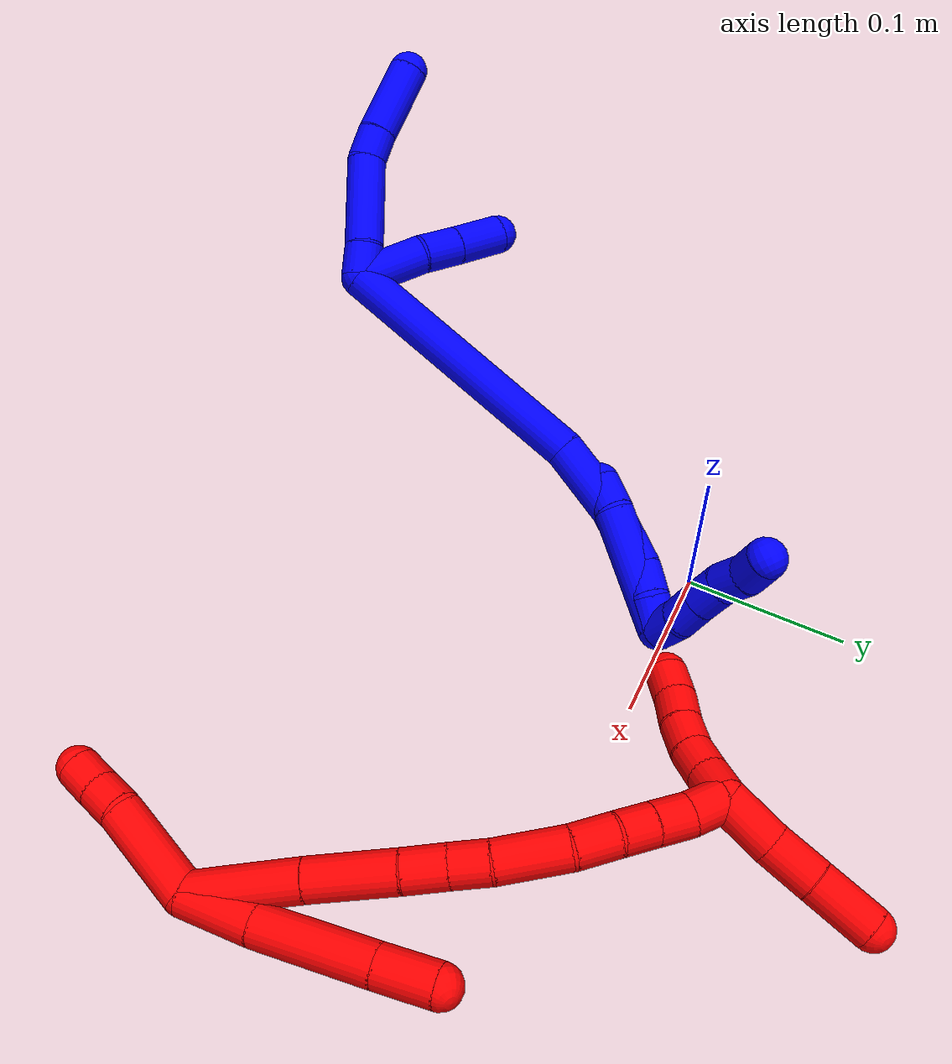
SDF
<sdf version="1.7">
 <world name="default">
  <plugin name="TubeGeneratorPlugin" filename="libtube_generator_plugin.so"/>
  <model name="photoneo_s_sensor">
   <static>1</static>
   <pose>0 0 2 1.57079 1.57079 3.14159</pose>
   <link name="link">
    <inertial><mass>0.1</mass></inertial>
    <sensor name="sensor" type="depth">
     <update_rate>30</update_rate>
     <camera>
      <horizontal_fov>1.22</horizontal_fov>
      <image><width>1920</width><height>1200</height><format>B8G8R8</format></image>
      <clip><near>0.1</near><far>4</far></clip>
      <depth_camera><output>points</output></depth_camera>
     </camera>
     <plugin name="camera_plugin" filename="libgazebo_ros_depth_camera.so">
      <baseline>0.2</baseline>
      <alwaysOn>1</alwaysOn>
      <updateRate>0.0</updateRate>
      <cameraName>camera_ir</cameraName>
      <imageTopicName>/camera/color/image_raw</imageTopicName>
      <cameraInfoTopicName>/camera/color/camera_info</cameraInfoTopicName>
      <depthImageTopicName>/camera/depth/image_raw</depthImageTopicName>
      <depthImageCameraInfoTopicName>/camera/depth/camera_info</depthImageCameraInfoTopicName>
      <pointCloudTopicName>/camera/depth/points</pointCloudTopicName>
      <frameName>fr_optical</frameName>
      <pointCloudCutoff>0.1</pointCloudCutoff>
      <pointCloudCutoffMax>2.0</pointCloudCutoffMax>
      <distortionK1>0</distortionK1>
      <distortionK2>0</distortionK2>
      <distortionK3>0</distortionK3>
      <distortionT1>0</distortionT1>
      <distortionT2>0</distortionT2>
      <CxPrime>0</CxPrime>
      <Cx>0</Cx>
      <Cy>0</Cy>
      <focalLength>0</focalLength>
      <hackBaseline>0</hackBaseline>
     </plugin>
    </sensor>
   </link>
  </model>
  <gravity>0 0 -9.8</gravity>
  <magnetic_field>6e-06 2.3e-05 -4.2e-05</magnetic_field>
  <atmosphere type="adiabatic"/>
  <physics name="default_physics" default="0" type="ode">
   <max_step_size>0.003</max_step_size>
   <real_time_factor>1</real_time_factor>
   <real_time_update_rate>1000</real_time_update_rate>
   <max_contacts>10000</max_contacts>
   <ode>
    <solver>
     <type>quick</type>
     <iters>100</iters>
     <sor>1.3</sor>
     <use_dynamic_moi_rescaling>0</use_dynamic_moi_rescaling>
    </solver>
    <constraints>
     <contact_max_correcting_vel>0</contact_max_correcting_vel>
     <contact_surface_layer>0.001</contact_surface_layer>
     <cfm>0</cfm>
     <erp>0.2</erp>
    </constraints>
   </ode>
  </physics>
  <scene><ambient>0.4 0.4 0.4 1</ambient><background>0.7 0.7 0.7 1</background><shadows>0</shadows></scene>
  <audio><device>default</device></audio>
  <spherical_coordinates>
   <surface_model>EARTH_WGS84</surface_model>
   <latitude_deg>0</latitude_deg>
   <longitude_deg>0</longitude_deg>
   <elevation>0</elevation>
   <heading_deg>0</heading_deg>
  </spherical_coordinates>
  <model name="bin">
   <static>1</static>
   <link name="bottom">
    <collision name="collision-bottom">
     <pose>0 0 -0.01 0 -0 0</pose>
     <geometry><box><size>0.8 0.6 0.02</size></box></geometry>
     <surface>
      <friction><ode><mu>100</mu><mu2>100</mu2></ode></friction>
      <contact><collide_bitmask>65535</collide_bitmask></contact>
     </surface>
    </collision>
   </link>
   <link name="west_wall">
    <collision name="collision-west_wall">
     <pose>-0.41 0 0.1 0 -0 0</pose>
     <geometry><box><size>0.02 0.6 0.2</size></box></geometry>
     <surface>
      <friction><ode><mu>100</mu><mu2>100</mu2></ode></friction>
      <contact><collide_bitmask>65535</collide_bitmask></contact>
     </surface>
    </collision>
   </link>
   <link name="east_wall">
    <collision name="collision-east_wall">
     <pose>0.41 0 0.1 0 -0 0</pose>
     <geometry><box><size>0.02 0.6 0.2</size></box></geometry>
     <surface>
      <friction><ode><mu>100</mu><mu2>100</mu2></ode></friction>
      <contact><collide_bitmask>65535</collide_bitmask></contact>
     </surface>
    </collision>
   </link>
   <link name="south_wall">
    <collision name="collision-south_wall">
     <pose>0 -0.31 0.1 0 -0 0</pose>
     <geometry><box><size>0.8 0.02 0.2</size></box></geometry>
     <surface>
      <friction><ode><mu>100</mu><mu2>100</mu2></ode></friction>
      <contact><collide_bitmask>65535</collide_bitmask></contact>
     </surface>
    </collision>
   </link>
   <link name="north_wall">
    <collision name="collision-north_wall">
     <pose>0 0.31 0.1 0 -0 0</pose>
     <geometry><box><size>0.8 0.02 0.2</size></box></geometry>
     <surface>
      <friction><ode><mu>100</mu><mu2>100</mu2></ode></friction>
      <contact><collide_bitmask>65535</collide_bitmask></contact>
     </surface>
    </collision>
   </link>
  </model>
  <model name="1">
   <static>0</static>
   <link name="1">
    <collision name="collision-cylinder-e_1_2_8">
     <pose>-0.001644 0.005099 0.008982 -0.516278 -0.157884 0.041767</pose>
     <geometry><cylinder><radius>0.0125</radius><length>0.020917</length></cylinder></geometry>
     <surface>
      <friction><ode><mu>1.16</mu><mu2>1.16</mu2><slip1>0</slip1><slip2>0</slip2></ode></friction>
      <contact><ode><kp>1e+06</kp><kd>1</kd><max_vel>0</max_vel><min_depth>0.001</min_depth></ode></contact>
     </surface>
    </collision>
    <visual name="visual-cylinder-e_1_2_8">
     <pose>-0.001644 0.005099 0.008982 -0.516278 -0.157884 0.041767</pose>
     <geometry><cylinder><radius>0.0125</radius><length>0.020917</length></cylinder></geometry>
     <material><ambient>0 0 1 1</ambient></material>
    </visual>
    <collision name="collision-cylinder-e_2_8_9">
     <pose>-0.010523 0.02154 0.044593 -0.4027 -0.244908 0.05023</pose>
     <geometry><cylinder><radius>0.0125</radius><length>0.059669</length></cylinder></geometry>
     <surface>
      <friction><ode><mu>1.16</mu><mu2>1.16</mu2><slip1>0</slip1><slip2>0</slip2></ode></friction>
      <contact><ode><kp>1e+06</kp><kd>1</kd><max_vel>0</max_vel><min_depth>0.001</min_depth></ode></contact>
     </surface>
    </collision>
    <visual name="visual-cylinder-e_2_8_9">
     <pose>-0.010523 0.02154 0.044593 -0.4027 -0.244908 0.05023</pose>
     <geometry><cylinder><radius>0.0125</radius><length>0.059669</length></cylinder></geometry>
     <material><ambient>0 0 1 1</ambient></material>
    </visual>
    <collision name="collision-cylinder-e_3_9_10">
     <pose>-0.020321 0.039588 0.078591 -0.738207 -0.251938 0.097898</pose>
     <geometry><cylinder><radius>0.0125</radius><length>0.020574</length></cylinder></geometry>
     <surface>
      <friction><ode><mu>1.16</mu><mu2>1.16</mu2><slip1>0</slip1><slip2>0</slip2></ode></friction>
      <contact><ode><kp>1e+06</kp><kd>1</kd><max_vel>0</max_vel><min_depth>0.001</min_depth></ode></contact>
     </surface>
    </collision>
    <visual name="visual-cylinder-e_3_9_10">
     <pose>-0.020321 0.039588 0.078591 -0.738207 -0.251938 0.097898</pose>
     <geometry><cylinder><radius>0.0125</radius><length>0.020574</length></cylinder></geometry>
     <material><ambient>0 0 1 1</ambient></material>
    </visual>
    <collision name="collision-cylinder-e_4_10_6">
     <pose>-0.03034 0.063347 0.101768 -0.823302 -0.310242 0.136336</pose>
     <geometry><cylinder><radius>0.0125</radius><length>0.04884</length></cylinder></geometry>
     <surface>
      <friction><ode><mu>1.16</mu><mu2>1.16</mu2><slip1>0</slip1><slip2>0</slip2></ode></friction>
      <contact><ode><kp>1e+06</kp><kd>1</kd><max_vel>0</max_vel><min_depth>0.001</min_depth></ode></contact>
     </surface>
    </collision>
    <visual name="visual-cylinder-e_4_10_6">
     <pose>-0.03034 0.063347 0.101768 -0.823302 -0.310242 0.136336</pose>
     <geometry><cylinder><radius>0.0125</radius><length>0.04884</length></cylinder></geometry>
     <material><ambient>0 0 1 1</ambient></material>
    </visual>
    <collision name="collision-cylinder-e_1_2_11">
     <pose>-0.009751 0.01918 -0.000276 -1.58519 -0.470321 0.476886</pose>
     <geometry><cylinder><radius>0.0125</radius><length>0.043036</length></cylinder></geometry>
     <surface>
      <friction><ode><mu>1.16</mu><mu2>1.16</mu2><slip1>0</slip1><slip2>0</slip2></ode></friction>
      <contact><ode><kp>1e+06</kp><kd>1</kd><max_vel>0</max_vel><min_depth>0.001</min_depth></ode></contact>
     </surface>
    </collision>
    <visual name="visual-cylinder-e_1_2_11">
     <pose>-0.009751 0.01918 -0.000276 -1.58519 -0.470321 0.476886</pose>
     <geometry><cylinder><radius>0.0125</radius><length>0.043036</length></cylinder></geometry>
     <material><ambient>0 0 1 1</ambient></material>
    </visual>
    <collision name="collision-cylinder-e_2_11_12">
     <pose>-0.027144 0.048362 -0.001509 -1.66617 -0.650146 0.710186</pose>
     <geometry><cylinder><radius>0.0125</radius><length>0.025247</length></cylinder></geometry>
     <surface>
      <friction><ode><mu>1.16</mu><mu2>1.16</mu2><slip1>0</slip1><slip2>0</slip2></ode></friction>
      <contact><ode><kp>1e+06</kp><kd>1</kd><max_vel>0</max_vel><min_depth>0.001</min_depth></ode></contact>
     </surface>
    </collision>
    <visual name="visual-cylinder-e_2_11_12">
     <pose>-0.027144 0.048362 -0.001509 -1.66617 -0.650146 0.710186</pose>
     <geometry><cylinder><radius>0.0125</radius><length>0.025247</length></cylinder></geometry>
     <material><ambient>0 0 1 1</ambient></material>
    </visual>
    <collision name="collision-cylinder-e_3_12_5">
     <pose>-0.044297 0.071025 -0.003317 -1.6379 -0.643269 0.684637</pose>
     <geometry><cylinder><radius>0.0125</radius><length>0.031717</length></cylinder></geometry>
     <surface>
      <friction><ode><mu>1.16</mu><mu2>1.16</mu2><slip1>0</slip1><slip2>0</slip2></ode></friction>
      <contact><ode><kp>1e+06</kp><kd>1</kd><max_vel>0</max_vel><min_depth>0.001</min_depth></ode></contact>
     </surface>
    </collision>
    <visual name="visual-cylinder-e_3_12_5">
     <pose>-0.044297 0.071025 -0.003317 -1.6379 -0.643269 0.684637</pose>
     <geometry><cylinder><radius>0.0125</radius><length>0.031717</length></cylinder></geometry>
     <material><ambient>0 0 1 1</ambient></material>
    </visual>
    <collision name="collision-cylinder-e_1_2_13">
     <pose>-0.009816 0.033359 -0.077645 -2.7358 -0.115642 0.548563</pose>
     <geometry><cylinder><radius>0.0125</radius><length>0.170152</length></cylinder></geometry>
     <surface>
      <friction><ode><mu>1.16</mu><mu2>1.16</mu2><slip1>0</slip1><slip2>0</slip2></ode></friction>
      <contact><ode><kp>1e+06</kp><kd>1</kd><max_vel>0</max_vel><min_depth>0.001</min_depth></ode></contact>
     </surface>
    </collision>
    <visual name="visual-cylinder-e_1_2_13">
     <pose>-0.009816 0.033359 -0.077645 -2.7358 -0.115642 0.548563</pose>
     <geometry><cylinder><radius>0.0125</radius><length>0.170152</length></cylinder></geometry>
     <material><ambient>0 0 1 1</ambient></material>
    </visual>
    <collision name="collision-cylinder-e_2_13_14">
     <pose>-0.017525 0.072059 -0.17929 -2.9226 0.085531 -0.742397</pose>
     <geometry><cylinder><radius>0.0125</radius><length>0.049354</length></cylinder></geometry>
     <surface>
      <friction><ode><mu>1.16</mu><mu2>1.16</mu2><slip1>0</slip1><slip2>0</slip2></ode></friction>
      <contact><ode><kp>1e+06</kp><kd>1</kd><max_vel>0</max_vel><min_depth>0.001</min_depth></ode></contact>
     </surface>
    </collision>
    <visual name="visual-cylinder-e_2_13_14">
     <pose>-0.017525 0.072059 -0.17929 -2.9226 0.085531 -0.742397</pose>
     <geometry><cylinder><radius>0.0125</radius><length>0.049354</length></cylinder></geometry>
     <material><ambient>0 0 1 1</ambient></material>
    </visual>
    <collision name="collision-cylinder-e_3_14_15">
     <pose>-0.013379 0.077918 -0.213075 -3.08882 0.205008 -2.63928</pose>
     <geometry><cylinder><radius>0.0125</radius><length>0.020018</length></cylinder></geometry>
     <surface>
      <friction><ode><mu>1.16</mu><mu2>1.16</mu2><slip1>0</slip1><slip2>0</slip2></ode></friction>
      <contact><ode><kp>1e+06</kp><kd>1</kd><max_vel>0</max_vel><min_depth>0.001</min_depth></ode></contact>
     </surface>
    </collision>
    <visual name="visual-cylinder-e_3_14_15">
     <pose>-0.013379 0.077918 -0.213075 -3.08882 0.205008 -2.63928</pose>
     <geometry><cylinder><radius>0.0125</radius><length>0.020018</length></cylinder></geometry>
     <material><ambient>0 0 1 1</ambient></material>
    </visual>
    <collision name="collision-cylinder-e_4_15_16">
     <pose>-0.009313 0.078923 -0.232707 -3.09205 0.20297 -2.66427</pose>
     <geometry><cylinder><radius>0.0125</radius><length>0.02013</length></cylinder></geometry>
     <surface>
      <friction><ode><mu>1.16</mu><mu2>1.16</mu2><slip1>0</slip1><slip2>0</slip2></ode></friction>
      <contact><ode><kp>1e+06</kp><kd>1</kd><max_vel>0</max_vel><min_depth>0.001</min_depth></ode></contact>
     </surface>
    </collision>
    <visual name="visual-cylinder-e_4_15_16">
     <pose>-0.009313 0.078923 -0.232707 -3.09205 0.20297 -2.66427</pose>
     <geometry><cylinder><radius>0.0125</radius><length>0.02013</length></cylinder></geometry>
     <material><ambient>0 0 1 1</ambient></material>
    </visual>
    <collision name="collision-cylinder-e_5_16_17">
     <pose>-0.003584 0.078333 -0.251913 3.02692 0.37421 2.55286</pose>
     <geometry><cylinder><radius>0.0125</radius><length>0.020243</length></cylinder></geometry>
     <surface>
      <friction><ode><mu>1.16</mu><mu2>1.16</mu2><slip1>0</slip1><slip2>0</slip2></ode></friction>
      <contact><ode><kp>1e+06</kp><kd>1</kd><max_vel>0</max_vel><min_depth>0.001</min_depth></ode></contact>
     </surface>
    </collision>
    <visual name="visual-cylinder-e_5_16_17">
     <pose>-0.003584 0.078333 -0.251913 3.02692 0.37421 2.55286</pose>
     <geometry><cylinder><radius>0.0125</radius><length>0.020243</length></cylinder></geometry>
     <material><ambient>0 0 1 1</ambient></material>
    </visual>
    <collision name="collision-cylinder-e_6_17_1">
     <pose>0.001116 0.075413 -0.271102 2.95633 0.099715 0.98581</pose>
     <geometry><cylinder><radius>0.0125</radius><length>0.020102</length></cylinder></geometry>
     <surface>
      <friction><ode><mu>1.16</mu><mu2>1.16</mu2><slip1>0</slip1><slip2>0</slip2></ode></friction>
      <contact><ode><kp>1e+06</kp><kd>1</kd><max_vel>0</max_vel><min_depth>0.001</min_depth></ode></contact>
     </surface>
    </collision>
    <visual name="visual-cylinder-e_6_17_1">
     <pose>0.001116 0.075413 -0.271102 2.95633 0.099715 0.98581</pose>
     <geometry><cylinder><radius>0.0125</radius><length>0.020102</length></cylinder></geometry>
     <material><ambient>0 0 1 1</ambient></material>
    </visual>
    <collision name="collision-cylinder-e_1_1_18">
     <pose>-0.004969 0.076247 -0.242665 -0.069827 -0.18266 0.006398</pose>
     <geometry><cylinder><radius>0.0125</radius><length>0.078019</length></cylinder></geometry>
     <surface>
      <friction><ode><mu>1.16</mu><mu2>1.16</mu2><slip1>0</slip1><slip2>0</slip2></ode></friction>
      <contact><ode><kp>1e+06</kp><kd>1</kd><max_vel>0</max_vel><min_depth>0.001</min_depth></ode></contact>
     </surface>
    </collision>
    <visual name="visual-cylinder-e_1_1_18">
     <pose>-0.004969 0.076247 -0.242665 -0.069827 -0.18266 0.006398</pose>
     <geometry><cylinder><radius>0.0125</radius><length>0.078019</length></cylinder></geometry>
     <material><ambient>0 0 1 1</ambient></material>
    </visual>
    <collision name="collision-cylinder-e_2_18_4">
     <pose>-0.016151 0.078356 -0.194215 0.05562 -0.381912 -0.010755</pose>
     <geometry><cylinder><radius>0.0125</radius><length>0.021981</length></cylinder></geometry>
     <surface>
      <friction><ode><mu>1.16</mu><mu2>1.16</mu2><slip1>0</slip1><slip2>0</slip2></ode></friction>
      <contact><ode><kp>1e+06</kp><kd>1</kd><max_vel>0</max_vel><min_depth>0.001</min_depth></ode></contact>
     </surface>
    </collision>
    <visual name="visual-cylinder-e_2_18_4">
     <pose>-0.016151 0.078356 -0.194215 0.05562 -0.381912 -0.010755</pose>
     <geometry><cylinder><radius>0.0125</radius><length>0.021981</length></cylinder></geometry>
     <material><ambient>0 0 1 1</ambient></material>
    </visual>
    <collision name="collision-cylinder-e_1_1_19">
     <pose>0.007971 0.081662 -0.280419 -1.50739 0.625361 -0.589167</pose>
     <geometry><cylinder><radius>0.0125</radius><length>0.02</length></cylinder></geometry>
     <surface>
      <friction><ode><mu>1.16</mu><mu2>1.16</mu2><slip1>0</slip1><slip2>0</slip2></ode></friction>
      <contact><ode><kp>1e+06</kp><kd>1</kd><max_vel>0</max_vel><min_depth>0.001</min_depth></ode></contact>
     </surface>
    </collision>
    <visual name="visual-cylinder-e_1_1_19">
     <pose>0.007971 0.081662 -0.280419 -1.50739 0.625361 -0.589167</pose>
     <geometry><cylinder><radius>0.0125</radius><length>0.02</length></cylinder></geometry>
     <material><ambient>0 0 1 1</ambient></material>
    </visual>
    <collision name="collision-cylinder-e_2_19_20">
     <pose>0.018528 0.098278 -0.277621 -1.30905 0.489612 -0.378807</pose>
     <geometry><cylinder><radius>0.0125</radius><length>0.02</length></cylinder></geometry>
     <surface>
      <friction><ode><mu>1.16</mu><mu2>1.16</mu2><slip1>0</slip1><slip2>0</slip2></ode></friction>
      <contact><ode><kp>1e+06</kp><kd>1</kd><max_vel>0</max_vel><min_depth>0.001</min_depth></ode></contact>
     </surface>
    </collision>
    <visual name="visual-cylinder-e_2_19_20">
     <pose>0.018528 0.098278 -0.277621 -1.30905 0.489612 -0.378807</pose>
     <geometry><cylinder><radius>0.0125</radius><length>0.02</length></cylinder></geometry>
     <material><ambient>0 0 1 1</ambient></material>
    </visual>
    <collision name="collision-cylinder-e_3_20_21">
     <pose>0.027996 0.115396 -0.273485 -1.35851 0.49669 -0.403913</pose>
     <geometry><cylinder><radius>0.0125</radius><length>0.02</length></cylinder></geometry>
     <surface>
      <friction><ode><mu>1.16</mu><mu2>1.16</mu2><slip1>0</slip1><slip2>0</slip2></ode></friction>
      <contact><ode><kp>1e+06</kp><kd>1</kd><max_vel>0</max_vel><min_depth>0.001</min_depth></ode></contact>
     </surface>
    </collision>
    <visual name="visual-cylinder-e_3_20_21">
     <pose>0.027996 0.115396 -0.273485 -1.35851 0.49669 -0.403913</pose>
     <geometry><cylinder><radius>0.0125</radius><length>0.02</length></cylinder></geometry>
     <material><ambient>0 0 1 1</ambient></material>
    </visual>
    <collision name="collision-cylinder-e_4_21_22">
     <pose>0.038646 0.132064 -0.272063 -1.62406 0.629228 -0.661268</pose>
     <geometry><cylinder><radius>0.0125</radius><length>0.02</length></cylinder></geometry>
     <surface>
      <friction><ode><mu>1.16</mu><mu2>1.16</mu2><slip1>0</slip1><slip2>0</slip2></ode></friction>
      <contact><ode><kp>1e+06</kp><kd>1</kd><max_vel>0</max_vel><min_depth>0.001</min_depth></ode></contact>
     </surface>
    </collision>
    <visual name="visual-cylinder-e_4_21_22">
     <pose>0.038646 0.132064 -0.272063 -1.62406 0.629228 -0.661268</pose>
     <geometry><cylinder><radius>0.0125</radius><length>0.02</length></cylinder></geometry>
     <material><ambient>0 0 1 1</ambient></material>
    </visual>
    <collision name="collision-cylinder-e_5_22_3">
     <pose>0.051249 0.147289 -0.270561 -1.30687 0.736581 -0.574572</pose>
     <geometry><cylinder><radius>0.0125</radius><length>0.02</length></cylinder></geometry>
     <surface>
      <friction><ode><mu>1.16</mu><mu2>1.16</mu2><slip1>0</slip1><slip2>0</slip2></ode></friction>
      <contact><ode><kp>1e+06</kp><kd>1</kd><max_vel>0</max_vel><min_depth>0.001</min_depth></ode></contact>
     </surface>
    </collision>
    <visual name="visual-cylinder-e_5_22_3">
     <pose>0.051249 0.147289 -0.270561 -1.30687 0.736581 -0.574572</pose>
     <geometry><cylinder><radius>0.0125</radius><length>0.02</length></cylinder></geometry>
     <material><ambient>0 0 1 1</ambient></material>
    </visual>
    <collision name="collision-sphere-3">
     <pose>0.057966 0.15444 -0.268629 0 -0 0</pose>
     <geometry><sphere><radius>0.0125</radius></sphere></geometry>
     <surface>
      <friction><ode><mu>1.16</mu><mu2>1.16</mu2><slip1>0</slip1><slip2>0</slip2></ode></friction>
      <contact><ode><kp>1e+06</kp><kd>1</kd><max_vel>0</max_vel><min_depth>0.001</min_depth></ode></contact>
     </surface>
    </collision>
    <visual name="visual-sphere-3">
     <pose>0.057966 0.15444 -0.268629 0 -0 0</pose>
     <geometry><sphere><radius>0.0125</radius></sphere></geometry>
     <material><ambient>0 0 1 1</ambient></material>
    </visual>
    <collision name="collision-sphere-22">
     <pose>0.044531 0.140137 -0.272494 0 -0 0</pose>
     <geometry><sphere><radius>0.0125</radius></sphere></geometry>
     <surface>
      <friction><ode><mu>1.16</mu><mu2>1.16</mu2><slip1>0</slip1><slip2>0</slip2></ode></friction>
      <contact><ode><kp>1e+06</kp><kd>1</kd><max_vel>0</max_vel><min_depth>0.001</min_depth></ode></contact>
     </surface>
    </collision>
    <visual name="visual-sphere-22">
     <pose>0.044531 0.140137 -0.272494 0 -0 0</pose>
     <geometry><sphere><radius>0.0125</radius></sphere></geometry>
     <material><ambient>0 0 1 1</ambient></material>
    </visual>
    <collision name="collision-sphere-21">
     <pose>0.032761 0.123991 -0.271633 0 -0 0</pose>
     <geometry><sphere><radius>0.0125</radius></sphere></geometry>
     <surface>
      <friction><ode><mu>1.16</mu><mu2>1.16</mu2><slip1>0</slip1><slip2>0</slip2></ode></friction>
      <contact><ode><kp>1e+06</kp><kd>1</kd><max_vel>0</max_vel><min_depth>0.001</min_depth></ode></contact>
     </surface>
    </collision>
    <visual name="visual-sphere-21">
     <pose>0.032761 0.123991 -0.271633 0 -0 0</pose>
     <geometry><sphere><radius>0.0125</radius></sphere></geometry>
     <material><ambient>0 0 1 1</ambient></material>
    </visual>
    <collision name="collision-sphere-20">
     <pose>0.02323 0.106802 -0.275338 0 -0 0</pose>
     <geometry><sphere><radius>0.0125</radius></sphere></geometry>
     <surface>
      <friction><ode><mu>1.16</mu><mu2>1.16</mu2><slip1>0</slip1><slip2>0</slip2></ode></friction>
      <contact><ode><kp>1e+06</kp><kd>1</kd><max_vel>0</max_vel><min_depth>0.001</min_depth></ode></contact>
     </surface>
    </collision>
    <visual name="visual-sphere-20">
     <pose>0.02323 0.106802 -0.275338 0 -0 0</pose>
     <geometry><sphere><radius>0.0125</radius></sphere></geometry>
     <material><ambient>0 0 1 1</ambient></material>
    </visual>
    <collision name="collision-sphere-19">
     <pose>0.013825 0.089753 -0.279905 0 -0 0</pose>
     <geometry><sphere><radius>0.0125</radius></sphere></geometry>
     <surface>
      <friction><ode><mu>1.16</mu><mu2>1.16</mu2><slip1>0</slip1><slip2>0</slip2></ode></friction>
      <contact><ode><kp>1e+06</kp><kd>1</kd><max_vel>0</max_vel><min_depth>0.001</min_depth></ode></contact>
     </surface>
    </collision>
    <visual name="visual-sphere-19">
     <pose>0.013825 0.089753 -0.279905 0 -0 0</pose>
     <geometry><sphere><radius>0.0125</radius></sphere></geometry>
     <material><ambient>0 0 1 1</ambient></material>
    </visual>
    <collision name="collision-sphere-11">
     <pose>-0.019503 0.038359 -0.000552 0 -0 0</pose>
     <geometry><sphere><radius>0.0125</radius></sphere></geometry>
     <surface>
      <friction><ode><mu>1.16</mu><mu2>1.16</mu2><slip1>0</slip1><slip2>0</slip2></ode></friction>
      <contact><ode><kp>1e+06</kp><kd>1</kd><max_vel>0</max_vel><min_depth>0.001</min_depth></ode></contact>
     </surface>
    </collision>
    <visual name="visual-sphere-11">
     <pose>-0.019503 0.038359 -0.000552 0 -0 0</pose>
     <geometry><sphere><radius>0.0125</radius></sphere></geometry>
     <material><ambient>0 0 1 1</ambient></material>
    </visual>
    <collision name="collision-sphere-6">
     <pose>-0.037796 0.080401 0.117576 0 -0 0</pose>
     <geometry><sphere><radius>0.0125</radius></sphere></geometry>
     <surface>
      <friction><ode><mu>1.16</mu><mu2>1.16</mu2><slip1>0</slip1><slip2>0</slip2></ode></friction>
      <contact><ode><kp>1e+06</kp><kd>1</kd><max_vel>0</max_vel><min_depth>0.001</min_depth></ode></contact>
     </surface>
    </collision>
    <visual name="visual-sphere-6">
     <pose>-0.037796 0.080401 0.117576 0 -0 0</pose>
     <geometry><sphere><radius>0.0125</radius></sphere></geometry>
     <material><ambient>0 0 1 1</ambient></material>
    </visual>
    <collision name="collision-sphere-10">
     <pose>-0.022885 0.046292 0.08596 0 -0 0</pose>
     <geometry><sphere><radius>0.0125</radius></sphere></geometry>
     <surface>
      <friction><ode><mu>1.16</mu><mu2>1.16</mu2><slip1>0</slip1><slip2>0</slip2></ode></friction>
      <contact><ode><kp>1e+06</kp><kd>1</kd><max_vel>0</max_vel><min_depth>0.001</min_depth></ode></contact>
     </surface>
    </collision>
    <visual name="visual-sphere-10">
     <pose>-0.022885 0.046292 0.08596 0 -0 0</pose>
     <geometry><sphere><radius>0.0125</radius></sphere></geometry>
     <material><ambient>0 0 1 1</ambient></material>
    </visual>
    <collision name="collision-sphere-9">
     <pose>-0.017756 0.032884 0.071222 0 -0 0</pose>
     <geometry><sphere><radius>0.0125</radius></sphere></geometry>
     <surface>
      <friction><ode><mu>1.16</mu><mu2>1.16</mu2><slip1>0</slip1><slip2>0</slip2></ode></friction>
      <contact><ode><kp>1e+06</kp><kd>1</kd><max_vel>0</max_vel><min_depth>0.001</min_depth></ode></contact>
     </surface>
    </collision>
    <visual name="visual-sphere-9">
     <pose>-0.017756 0.032884 0.071222 0 -0 0</pose>
     <geometry><sphere><radius>0.0125</radius></sphere></geometry>
     <material><ambient>0 0 1 1</ambient></material>
    </visual>
    <collision name="collision-sphere-2">
     <geometry><sphere><radius>0.0125</radius></sphere></geometry>
     <surface>
      <friction><ode><mu>1.16</mu><mu2>1.16</mu2><slip1>0</slip1><slip2>0</slip2></ode></friction>
      <contact><ode><kp>1e+06</kp><kd>1</kd><max_vel>0</max_vel><min_depth>0.001</min_depth></ode></contact>
     </surface>
    </collision>
    <visual name="visual-sphere-2">
     <geometry><sphere><radius>0.0125</radius></sphere></geometry>
     <material><ambient>0 0 1 1</ambient></material>
    </visual>
    <collision name="collision-sphere-8">
     <pose>-0.003289 0.010197 0.017964 0 -0 0</pose>
     <geometry><sphere><radius>0.0125</radius></sphere></geometry>
     <surface>
      <friction><ode><mu>1.16</mu><mu2>1.16</mu2><slip1>0</slip1><slip2>0</slip2></ode></friction>
      <contact><ode><kp>1e+06</kp><kd>1</kd><max_vel>0</max_vel><min_depth>0.001</min_depth></ode></contact>
     </surface>
    </collision>
    <visual name="visual-sphere-8">
     <pose>-0.003289 0.010197 0.017964 0 -0 0</pose>
     <geometry><sphere><radius>0.0125</radius></sphere></geometry>
     <material><ambient>0 0 1 1</ambient></material>
    </visual>
    <collision name="collision-sphere-12">
     <pose>-0.034785 0.058364 -0.002466 0 -0 0</pose>
     <geometry><sphere><radius>0.0125</radius></sphere></geometry>
     <surface>
      <friction><ode><mu>1.16</mu><mu2>1.16</mu2><slip1>0</slip1><slip2>0</slip2></ode></friction>
      <contact><ode><kp>1e+06</kp><kd>1</kd><max_vel>0</max_vel><min_depth>0.001</min_depth></ode></contact>
     </surface>
    </collision>
    <visual name="visual-sphere-12">
     <pose>-0.034785 0.058364 -0.002466 0 -0 0</pose>
     <geometry><sphere><radius>0.0125</radius></sphere></geometry>
     <material><ambient>0 0 1 1</ambient></material>
    </visual>
    <collision name="collision-sphere-5">
     <pose>-0.053809 0.083685 -0.004168 0 -0 0</pose>
     <geometry><sphere><radius>0.0125</radius></sphere></geometry>
     <surface>
      <friction><ode><mu>1.16</mu><mu2>1.16</mu2><slip1>0</slip1><slip2>0</slip2></ode></friction>
      <contact><ode><kp>1e+06</kp><kd>1</kd><max_vel>0</max_vel><min_depth>0.001</min_depth></ode></contact>
     </surface>
    </collision>
    <visual name="visual-sphere-5">
     <pose>-0.053809 0.083685 -0.004168 0 -0 0</pose>
     <geometry><sphere><radius>0.0125</radius></sphere></geometry>
     <material><ambient>0 0 1 1</ambient></material>
    </visual>
    <collision name="collision-sphere-13">
     <pose>-0.019633 0.066718 -0.15529 0 -0 0</pose>
     <geometry><sphere><radius>0.0125</radius></sphere></geometry>
     <surface>
      <friction><ode><mu>1.16</mu><mu2>1.16</mu2><slip1>0</slip1><slip2>0</slip2></ode></friction>
      <contact><ode><kp>1e+06</kp><kd>1</kd><max_vel>0</max_vel><min_depth>0.001</min_depth></ode></contact>
     </surface>
    </collision>
    <visual name="visual-sphere-13">
     <pose>-0.019633 0.066718 -0.15529 0 -0 0</pose>
     <geometry><sphere><radius>0.0125</radius></sphere></geometry>
     <material><ambient>0 0 1 1</ambient></material>
    </visual>
    <collision name="collision-sphere-14">
     <pose>-0.015417 0.077401 -0.20329 0 -0 0</pose>
     <geometry><sphere><radius>0.0125</radius></sphere></geometry>
     <surface>
      <friction><ode><mu>1.16</mu><mu2>1.16</mu2><slip1>0</slip1><slip2>0</slip2></ode></friction>
      <contact><ode><kp>1e+06</kp><kd>1</kd><max_vel>0</max_vel><min_depth>0.001</min_depth></ode></contact>
     </surface>
    </collision>
    <visual name="visual-sphere-14">
     <pose>-0.015417 0.077401 -0.20329 0 -0 0</pose>
     <geometry><sphere><radius>0.0125</radius></sphere></geometry>
     <material><ambient>0 0 1 1</ambient></material>
    </visual>
    <collision name="collision-sphere-15">
     <pose>-0.011342 0.078435 -0.222861 0 -0 0</pose>
     <geometry><sphere><radius>0.0125</radius></sphere></geometry>
     <surface>
      <friction><ode><mu>1.16</mu><mu2>1.16</mu2><slip1>0</slip1><slip2>0</slip2></ode></friction>
      <contact><ode><kp>1e+06</kp><kd>1</kd><max_vel>0</max_vel><min_depth>0.001</min_depth></ode></contact>
     </surface>
    </collision>
    <visual name="visual-sphere-15">
     <pose>-0.011342 0.078435 -0.222861 0 -0 0</pose>
     <geometry><sphere><radius>0.0125</radius></sphere></geometry>
     <material><ambient>0 0 1 1</ambient></material>
    </visual>
    <collision name="collision-sphere-16">
     <pose>-0.007284 0.079411 -0.242554 0 -0 0</pose>
     <geometry><sphere><radius>0.0125</radius></sphere></geometry>
     <surface>
      <friction><ode><mu>1.16</mu><mu2>1.16</mu2><slip1>0</slip1><slip2>0</slip2></ode></friction>
      <contact><ode><kp>1e+06</kp><kd>1</kd><max_vel>0</max_vel><min_depth>0.001</min_depth></ode></contact>
     </surface>
    </collision>
    <visual name="visual-sphere-16">
     <pose>-0.007284 0.079411 -0.242554 0 -0 0</pose>
     <geometry><sphere><radius>0.0125</radius></sphere></geometry>
     <material><ambient>0 0 1 1</ambient></material>
    </visual>
    <collision name="collision-sphere-17">
     <pose>0.000116 0.077255 -0.261272 0 -0 0</pose>
     <geometry><sphere><radius>0.0125</radius></sphere></geometry>
     <surface>
      <friction><ode><mu>1.16</mu><mu2>1.16</mu2><slip1>0</slip1><slip2>0</slip2></ode></friction>
      <contact><ode><kp>1e+06</kp><kd>1</kd><max_vel>0</max_vel><min_depth>0.001</min_depth></ode></contact>
     </surface>
    </collision>
    <visual name="visual-sphere-17">
     <pose>0.000116 0.077255 -0.261272 0 -0 0</pose>
     <geometry><sphere><radius>0.0125</radius></sphere></geometry>
     <material><ambient>0 0 1 1</ambient></material>
    </visual>
    <collision name="collision-sphere-1">
     <pose>0.002117 0.073571 -0.280932 0 -0 0</pose>
     <geometry><sphere><radius>0.0125</radius></sphere></geometry>
     <surface>
      <friction><ode><mu>1.16</mu><mu2>1.16</mu2><slip1>0</slip1><slip2>0</slip2></ode></friction>
      <contact><ode><kp>1e+06</kp><kd>1</kd><max_vel>0</max_vel><min_depth>0.001</min_depth></ode></contact>
     </surface>
    </collision>
    <visual name="visual-sphere-1">
     <pose>0.002117 0.073571 -0.280932 0 -0 0</pose>
     <geometry><sphere><radius>0.0125</radius></sphere></geometry>
     <material><ambient>0 0 1 1</ambient></material>
    </visual>
    <collision name="collision-sphere-18">
     <pose>-0.012055 0.078923 -0.204398 0 -0 0</pose>
     <geometry><sphere><radius>0.0125</radius></sphere></geometry>
     <surface>
      <friction><ode><mu>1.16</mu><mu2>1.16</mu2><slip1>0</slip1><slip2>0</slip2></ode></friction>
      <contact><ode><kp>1e+06</kp><kd>1</kd><max_vel>0</max_vel><min_depth>0.001</min_depth></ode></contact>
     </surface>
    </collision>
    <visual name="visual-sphere-18">
     <pose>-0.012055 0.078923 -0.204398 0 -0 0</pose>
     <geometry><sphere><radius>0.0125</radius></sphere></geometry>
     <material><ambient>0 0 1 1</ambient></material>
    </visual>
    <collision name="collision-sphere-4">
     <pose>-0.020247 0.07779 -0.184032 0 -0 0</pose>
     <geometry><sphere><radius>0.0125</radius></sphere></geometry>
     <surface>
      <friction><ode><mu>1.16</mu><mu2>1.16</mu2><slip1>0</slip1><slip2>0</slip2></ode></friction>
      <contact><ode><kp>1e+06</kp><kd>1</kd><max_vel>0</max_vel><min_depth>0.001</min_depth></ode></contact>
     </surface>
    </collision>
    <visual name="visual-sphere-4">
     <pose>-0.020247 0.07779 -0.184032 0 -0 0</pose>
     <geometry><sphere><radius>0.0125</radius></sphere></geometry>
     <material><ambient>0 0 1 1</ambient></material>
    </visual>
    <inertial>
     <pose>-0.007957 0.058996 -0.110617 0 -0 0</pose>
     <mass>0.75</mass>
     <inertia>
      <ixx>0.000663</ixx>
      <ixy>0</ixy>
      <ixz>0</ixz>
      <iyy>-2e-06</iyy>
      <iyz>0</iyz>
      <izz>-0.000142</izz>
     </inertia>
    </inertial>
   </link>
   <pose>-0.055394 -0.257273 0.10788 0.760082 -0.875114 0.061614</pose>
  </model>
  <model name="2">
   <static>0</static>
   <link name="2">
    <collision name="collision-cylinder-e_1_2_8">
     <pose>0.012264 0.005995 0.017486 -0.330293 0.585755 -0.100431</pose>
     <geometry><cylinder><radius>0.0125</radius><length>0.044366</length></cylinder></geometry>
     <surface>
      <friction><ode><mu>1.16</mu><mu2>1.16</mu2><slip1>0</slip1><slip2>0</slip2></ode></friction>
      <contact><ode><kp>1e+06</kp><kd>1</kd><max_vel>0</max_vel><min_depth>0.001</min_depth></ode></contact>
     </surface>
    </collision>
    <visual name="visual-cylinder-e_1_2_8">
     <pose>0.012264 0.005995 0.017486 -0.330293 0.585755 -0.100431</pose>
     <geometry><cylinder><radius>0.0125</radius><length>0.044366</length></cylinder></geometry>
     <material><ambient>1 0 0 1</ambient></material>
    </visual>
    <collision name="collision-cylinder-e_2_8_9">
     <pose>0.044277 0.02388 0.062023 -0.414113 0.58919 -0.127306</pose>
     <geometry><cylinder><radius>0.0125</radius><length>0.071082</length></cylinder></geometry>
     <surface>
      <friction><ode><mu>1.16</mu><mu2>1.16</mu2><slip1>0</slip1><slip2>0</slip2></ode></friction>
      <contact><ode><kp>1e+06</kp><kd>1</kd><max_vel>0</max_vel><min_depth>0.001</min_depth></ode></contact>
     </surface>
    </collision>
    <visual name="visual-cylinder-e_2_8_9">
     <pose>0.044277 0.02388 0.062023 -0.414113 0.58919 -0.127306</pose>
     <geometry><cylinder><radius>0.0125</radius><length>0.071082</length></cylinder></geometry>
     <material><ambient>1 0 0 1</ambient></material>
    </visual>
    <collision name="collision-cylinder-e_3_9_6">
     <pose>0.07368 0.041752 0.102091 -0.430747 0.592958 -0.13346</pose>
     <geometry><cylinder><radius>0.0125</radius><length>0.034552</length></cylinder></geometry>
     <surface>
      <friction><ode><mu>1.16</mu><mu2>1.16</mu2><slip1>0</slip1><slip2>0</slip2></ode></friction>
      <contact><ode><kp>1e+06</kp><kd>1</kd><max_vel>0</max_vel><min_depth>0.001</min_depth></ode></contact>
     </surface>
    </collision>
    <visual name="visual-cylinder-e_3_9_6">
     <pose>0.07368 0.041752 0.102091 -0.430747 0.592958 -0.13346</pose>
     <geometry><cylinder><radius>0.0125</radius><length>0.034552</length></cylinder></geometry>
     <material><ambient>1 0 0 1</ambient></material>
    </visual>
    <collision name="collision-cylinder-e_1_2_10">
     <pose>-0.013826 0.00548 -0.026 -2.93386 -0.479782 2.33586</pose>
     <geometry><cylinder><radius>0.0125</radius><length>0.059905</length></cylinder></geometry>
     <surface>
      <friction><ode><mu>1.16</mu><mu2>1.16</mu2><slip1>0</slip1><slip2>0</slip2></ode></friction>
      <contact><ode><kp>1e+06</kp><kd>1</kd><max_vel>0</max_vel><min_depth>0.001</min_depth></ode></contact>
     </surface>
    </collision>
    <visual name="visual-cylinder-e_1_2_10">
     <pose>-0.013826 0.00548 -0.026 -2.93386 -0.479782 2.33586</pose>
     <geometry><cylinder><radius>0.0125</radius><length>0.059905</length></cylinder></geometry>
     <material><ambient>1 0 0 1</ambient></material>
    </visual>
    <collision name="collision-cylinder-e_2_10_11">
     <pose>-0.031199 0.01057 -0.061369 3.09999 -0.36168 -2.915</pose>
     <geometry><cylinder><radius>0.0125</radius><length>0.020054</length></cylinder></geometry>
     <surface>
      <friction><ode><mu>1.16</mu><mu2>1.16</mu2><slip1>0</slip1><slip2>0</slip2></ode></friction>
      <contact><ode><kp>1e+06</kp><kd>1</kd><max_vel>0</max_vel><min_depth>0.001</min_depth></ode></contact>
     </surface>
    </collision>
    <visual name="visual-cylinder-e_2_10_11">
     <pose>-0.031199 0.01057 -0.061369 3.09999 -0.36168 -2.915</pose>
     <geometry><cylinder><radius>0.0125</radius><length>0.020054</length></cylinder></geometry>
     <material><ambient>1 0 0 1</ambient></material>
    </visual>
    <collision name="collision-cylinder-e_3_11_5">
     <pose>-0.038795 0.010461 -0.079902 -3.11091 -0.415828 2.99639</pose>
     <geometry><cylinder><radius>0.0125</radius><length>0.020041</length></cylinder></geometry>
     <surface>
      <friction><ode><mu>1.16</mu><mu2>1.16</mu2><slip1>0</slip1><slip2>0</slip2></ode></friction>
      <contact><ode><kp>1e+06</kp><kd>1</kd><max_vel>0</max_vel><min_depth>0.001</min_depth></ode></contact>
     </surface>
    </collision>
    <visual name="visual-cylinder-e_3_11_5">
     <pose>-0.038795 0.010461 -0.079902 -3.11091 -0.415828 2.99639</pose>
     <geometry><cylinder><radius>0.0125</radius><length>0.020041</length></cylinder></geometry>
     <material><ambient>1 0 0 1</ambient></material>
    </visual>
    <collision name="collision-cylinder-e_1_2_12">
     <pose>0.020137 0.021178 0.016933 -0.896307 0.638781 -0.31536</pose>
     <geometry><cylinder><radius>0.0125</radius><length>0.06755</length></cylinder></geometry>
     <surface>
      <friction><ode><mu>1.16</mu><mu2>1.16</mu2><slip1>0</slip1><slip2>0</slip2></ode></friction>
      <contact><ode><kp>1e+06</kp><kd>1</kd><max_vel>0</max_vel><min_depth>0.001</min_depth></ode></contact>
     </surface>
    </collision>
    <visual name="visual-cylinder-e_1_2_12">
     <pose>0.020137 0.021178 0.016933 -0.896307 0.638781 -0.31536</pose>
     <geometry><cylinder><radius>0.0125</radius><length>0.06755</length></cylinder></geometry>
     <material><ambient>1 0 0 1</ambient></material>
    </visual>
    <collision name="collision-cylinder-e_2_12_13">
     <pose>0.056305 0.058021 0.047131 -0.868233 0.66302 -0.316494</pose>
     <geometry><cylinder><radius>0.0125</radius><length>0.05209</length></cylinder></geometry>
     <surface>
      <friction><ode><mu>1.16</mu><mu2>1.16</mu2><slip1>0</slip1><slip2>0</slip2></ode></friction>
      <contact><ode><kp>1e+06</kp><kd>1</kd><max_vel>0</max_vel><min_depth>0.001</min_depth></ode></contact>
     </surface>
    </collision>
    <visual name="visual-cylinder-e_2_12_13">
     <pose>0.056305 0.058021 0.047131 -0.868233 0.66302 -0.316494</pose>
     <geometry><cylinder><radius>0.0125</radius><length>0.05209</length></cylinder></geometry>
     <material><ambient>1 0 0 1</ambient></material>
    </visual>
    <collision name="collision-cylinder-e_3_13_14">
     <pose>0.080996 0.081117 0.066055 -0.919765 0.747613 -0.383783</pose>
     <geometry><cylinder><radius>0.0125</radius><length>0.025475</length></cylinder></geometry>
     <surface>
      <friction><ode><mu>1.16</mu><mu2>1.16</mu2><slip1>0</slip1><slip2>0</slip2></ode></friction>
      <contact><ode><kp>1e+06</kp><kd>1</kd><max_vel>0</max_vel><min_depth>0.001</min_depth></ode></contact>
     </surface>
    </collision>
    <visual name="visual-cylinder-e_3_13_14">
     <pose>0.080996 0.081117 0.066055 -0.919765 0.747613 -0.383783</pose>
     <geometry><cylinder><radius>0.0125</radius><length>0.025475</length></cylinder></geometry>
     <material><ambient>1 0 0 1</ambient></material>
    </visual>
    <collision name="collision-cylinder-e_4_14_15">
     <pose>0.097018 0.095097 0.07698 -0.89374 0.719463 -0.356623</pose>
     <geometry><cylinder><radius>0.0125</radius><length>0.022343</length></cylinder></geometry>
     <surface>
      <friction><ode><mu>1.16</mu><mu2>1.16</mu2><slip1>0</slip1><slip2>0</slip2></ode></friction>
      <contact><ode><kp>1e+06</kp><kd>1</kd><max_vel>0</max_vel><min_depth>0.001</min_depth></ode></contact>
     </surface>
    </collision>
    <visual name="visual-cylinder-e_4_14_15">
     <pose>0.097018 0.095097 0.07698 -0.89374 0.719463 -0.356623</pose>
     <geometry><cylinder><radius>0.0125</radius><length>0.022343</length></cylinder></geometry>
     <material><ambient>1 0 0 1</ambient></material>
    </visual>
    <collision name="collision-cylinder-e_5_15_16">
     <pose>0.119337 0.114259 0.089557 -1.04535 0.798198 -0.476696</pose>
     <geometry><cylinder><radius>0.0125</radius><length>0.041775</length></cylinder></geometry>
     <surface>
      <friction><ode><mu>1.16</mu><mu2>1.16</mu2><slip1>0</slip1><slip2>0</slip2></ode></friction>
      <contact><ode><kp>1e+06</kp><kd>1</kd><max_vel>0</max_vel><min_depth>0.001</min_depth></ode></contact>
     </surface>
    </collision>
    <visual name="visual-cylinder-e_5_15_16">
     <pose>0.119337 0.114259 0.089557 -1.04535 0.798198 -0.476696</pose>
     <geometry><cylinder><radius>0.0125</radius><length>0.041775</length></cylinder></geometry>
     <material><ambient>1 0 0 1</ambient></material>
    </visual>
    <collision name="collision-cylinder-e_6_16_17">
     <pose>0.144233 0.134458 0.099218 -1.27075 0.896625 -0.681644</pose>
     <geometry><cylinder><radius>0.0125</radius><length>0.025443</length></cylinder></geometry>
     <surface>
      <friction><ode><mu>1.16</mu><mu2>1.16</mu2><slip1>0</slip1><slip2>0</slip2></ode></friction>
      <contact><ode><kp>1e+06</kp><kd>1</kd><max_vel>0</max_vel><min_depth>0.001</min_depth></ode></contact>
     </surface>
    </collision>
    <visual name="visual-cylinder-e_6_16_17">
     <pose>0.144233 0.134458 0.099218 -1.27075 0.896625 -0.681644</pose>
     <geometry><cylinder><radius>0.0125</radius><length>0.025443</length></cylinder></geometry>
     <material><ambient>1 0 0 1</ambient></material>
    </visual>
    <collision name="collision-cylinder-e_7_17_18">
     <pose>0.163161 0.147247 0.102394 -1.41275 1.0407 -0.909507</pose>
     <geometry><cylinder><radius>0.0125</radius><length>0.020841</length></cylinder></geometry>
     <surface>
      <friction><ode><mu>1.16</mu><mu2>1.16</mu2><slip1>0</slip1><slip2>0</slip2></ode></friction>
      <contact><ode><kp>1e+06</kp><kd>1</kd><max_vel>0</max_vel><min_depth>0.001</min_depth></ode></contact>
     </surface>
    </collision>
    <visual name="visual-cylinder-e_7_17_18">
     <pose>0.163161 0.147247 0.102394 -1.41275 1.0407 -0.909507</pose>
     <geometry><cylinder><radius>0.0125</radius><length>0.020841</length></cylinder></geometry>
     <material><ambient>1 0 0 1</ambient></material>
    </visual>
    <collision name="collision-cylinder-e_8_18_19">
     <pose>0.181958 0.158011 0.104149 -1.40592 1.04907 -0.911689</pose>
     <geometry><cylinder><radius>0.0125</radius><length>0.022622</length></cylinder></geometry>
     <surface>
      <friction><ode><mu>1.16</mu><mu2>1.16</mu2><slip1>0</slip1><slip2>0</slip2></ode></friction>
      <contact><ode><kp>1e+06</kp><kd>1</kd><max_vel>0</max_vel><min_depth>0.001</min_depth></ode></contact>
     </surface>
    </collision>
    <visual name="visual-cylinder-e_8_18_19">
     <pose>0.181958 0.158011 0.104149 -1.40592 1.04907 -0.911689</pose>
     <geometry><cylinder><radius>0.0125</radius><length>0.022622</length></cylinder></geometry>
     <material><ambient>1 0 0 1</ambient></material>
    </visual>
    <collision name="collision-cylinder-e_9_19_1">
     <pose>0.199506 0.17119 0.106302 -1.411 0.78707 -0.67982</pose>
     <geometry><cylinder><radius>0.0125</radius><length>0.021862</length></cylinder></geometry>
     <surface>
      <friction><ode><mu>1.16</mu><mu2>1.16</mu2><slip1>0</slip1><slip2>0</slip2></ode></friction>
      <contact><ode><kp>1e+06</kp><kd>1</kd><max_vel>0</max_vel><min_depth>0.001</min_depth></ode></contact>
     </surface>
    </collision>
    <visual name="visual-cylinder-e_9_19_1">
     <pose>0.199506 0.17119 0.106302 -1.411 0.78707 -0.67982</pose>
     <geometry><cylinder><radius>0.0125</radius><length>0.021862</length></cylinder></geometry>
     <material><ambient>1 0 0 1</ambient></material>
    </visual>
    <collision name="collision-cylinder-e_1_1_20">
     <pose>0.208692 0.179401 0.097652 -3.08167 0.144835 -2.35798</pose>
     <geometry><cylinder><radius>0.0125</radius><length>0.02</length></cylinder></geometry>
     <surface>
      <friction><ode><mu>1.16</mu><mu2>1.16</mu2><slip1>0</slip1><slip2>0</slip2></ode></friction>
      <contact><ode><kp>1e+06</kp><kd>1</kd><max_vel>0</max_vel><min_depth>0.001</min_depth></ode></contact>
     </surface>
    </collision>
    <visual name="visual-cylinder-e_1_1_20">
     <pose>0.208692 0.179401 0.097652 -3.08167 0.144835 -2.35798</pose>
     <geometry><cylinder><radius>0.0125</radius><length>0.02</length></cylinder></geometry>
     <material><ambient>1 0 0 1</ambient></material>
    </visual>
    <collision name="collision-cylinder-e_2_20_21">
     <pose>0.21098 0.181203 0.077884 -3.01989 0.084589 -1.21423</pose>
     <geometry><cylinder><radius>0.0125</radius><length>0.02</length></cylinder></geometry>
     <surface>
      <friction><ode><mu>1.16</mu><mu2>1.16</mu2><slip1>0</slip1><slip2>0</slip2></ode></friction>
      <contact><ode><kp>1e+06</kp><kd>1</kd><max_vel>0</max_vel><min_depth>0.001</min_depth></ode></contact>
     </surface>
    </collision>
    <visual name="visual-cylinder-e_2_20_21">
     <pose>0.21098 0.181203 0.077884 -3.01989 0.084589 -1.21423</pose>
     <geometry><cylinder><radius>0.0125</radius><length>0.02</length></cylinder></geometry>
     <material><ambient>1 0 0 1</ambient></material>
    </visual>
    <collision name="collision-cylinder-e_3_21_22">
     <pose>0.213328 0.185246 0.058522 -2.85091 0.150893 -0.953401</pose>
     <geometry><cylinder><radius>0.0125</radius><length>0.02</length></cylinder></geometry>
     <surface>
      <friction><ode><mu>1.16</mu><mu2>1.16</mu2><slip1>0</slip1><slip2>0</slip2></ode></friction>
      <contact><ode><kp>1e+06</kp><kd>1</kd><max_vel>0</max_vel><min_depth>0.001</min_depth></ode></contact>
     </surface>
    </collision>
    <visual name="visual-cylinder-e_3_21_22">
     <pose>0.213328 0.185246 0.058522 -2.85091 0.150893 -0.953401</pose>
     <geometry><cylinder><radius>0.0125</radius><length>0.02</length></cylinder></geometry>
     <material><ambient>1 0 0 1</ambient></material>
    </visual>
    <collision name="collision-cylinder-e_4_22_23">
     <pose>0.217424 0.191459 0.040003 -2.78411 0.262301 -1.2613</pose>
     <geometry><cylinder><radius>0.0125</radius><length>0.02</length></cylinder></geometry>
     <surface>
      <friction><ode><mu>1.16</mu><mu2>1.16</mu2><slip1>0</slip1><slip2>0</slip2></ode></friction>
      <contact><ode><kp>1e+06</kp><kd>1</kd><max_vel>0</max_vel><min_depth>0.001</min_depth></ode></contact>
     </surface>
    </collision>
    <visual name="visual-cylinder-e_4_22_23">
     <pose>0.217424 0.191459 0.040003 -2.78411 0.262301 -1.2613</pose>
     <geometry><cylinder><radius>0.0125</radius><length>0.02</length></cylinder></geometry>
     <material><ambient>1 0 0 1</ambient></material>
    </visual>
    <collision name="collision-cylinder-e_5_23_4">
     <pose>0.221513 0.198067 0.021609 -2.80901 0.150092 -0.842313</pose>
     <geometry><cylinder><radius>0.0125</radius><length>0.02</length></cylinder></geometry>
     <surface>
      <friction><ode><mu>1.16</mu><mu2>1.16</mu2><slip1>0</slip1><slip2>0</slip2></ode></friction>
      <contact><ode><kp>1e+06</kp><kd>1</kd><max_vel>0</max_vel><min_depth>0.001</min_depth></ode></contact>
     </surface>
    </collision>
    <visual name="visual-cylinder-e_5_23_4">
     <pose>0.221513 0.198067 0.021609 -2.80901 0.150092 -0.842313</pose>
     <geometry><cylinder><radius>0.0125</radius><length>0.02</length></cylinder></geometry>
     <material><ambient>1 0 0 1</ambient></material>
    </visual>
    <collision name="collision-cylinder-e_1_1_24">
     <pose>0.218135 0.174997 0.119757 0.302121 0.704514 0.111792</pose>
     <geometry><cylinder><radius>0.0125</radius><length>0.033619</length></cylinder></geometry>
     <surface>
      <friction><ode><mu>1.16</mu><mu2>1.16</mu2><slip1>0</slip1><slip2>0</slip2></ode></friction>
      <contact><ode><kp>1e+06</kp><kd>1</kd><max_vel>0</max_vel><min_depth>0.001</min_depth></ode></contact>
     </surface>
    </collision>
    <visual name="visual-cylinder-e_1_1_24">
     <pose>0.218135 0.174997 0.119757 0.302121 0.704514 0.111792</pose>
     <geometry><cylinder><radius>0.0125</radius><length>0.033619</length></cylinder></geometry>
     <material><ambient>1 0 0 1</ambient></material>
    </visual>
    <collision name="collision-cylinder-e_2_24_25">
     <pose>0.237442 0.169463 0.143828 0.144491 0.61306 0.045804</pose>
     <geometry><cylinder><radius>0.0125</radius><length>0.029266</length></cylinder></geometry>
     <surface>
      <friction><ode><mu>1.16</mu><mu2>1.16</mu2><slip1>0</slip1><slip2>0</slip2></ode></friction>
      <contact><ode><kp>1e+06</kp><kd>1</kd><max_vel>0</max_vel><min_depth>0.001</min_depth></ode></contact>
     </surface>
    </collision>
    <visual name="visual-cylinder-e_2_24_25">
     <pose>0.237442 0.169463 0.143828 0.144491 0.61306 0.045804</pose>
     <geometry><cylinder><radius>0.0125</radius><length>0.029266</length></cylinder></geometry>
     <material><ambient>1 0 0 1</ambient></material>
    </visual>
    <collision name="collision-cylinder-e_3_25_3">
     <pose>0.25737 0.165261 0.170017 0.171086 0.668974 0.059588</pose>
     <geometry><cylinder><radius>0.0125</radius><length>0.037115</length></cylinder></geometry>
     <surface>
      <friction><ode><mu>1.16</mu><mu2>1.16</mu2><slip1>0</slip1><slip2>0</slip2></ode></friction>
      <contact><ode><kp>1e+06</kp><kd>1</kd><max_vel>0</max_vel><min_depth>0.001</min_depth></ode></contact>
     </surface>
    </collision>
    <visual name="visual-cylinder-e_3_25_3">
     <pose>0.25737 0.165261 0.170017 0.171086 0.668974 0.059588</pose>
     <geometry><cylinder><radius>0.0125</radius><length>0.037115</length></cylinder></geometry>
     <material><ambient>1 0 0 1</ambient></material>
    </visual>
    <collision name="collision-sphere-3">
     <pose>0.268879 0.162783 0.184361 0 -0 0</pose>
     <geometry><sphere><radius>0.0125</radius></sphere></geometry>
     <surface>
      <friction><ode><mu>1.16</mu><mu2>1.16</mu2><slip1>0</slip1><slip2>0</slip2></ode></friction>
      <contact><ode><kp>1e+06</kp><kd>1</kd><max_vel>0</max_vel><min_depth>0.001</min_depth></ode></contact>
     </surface>
    </collision>
    <visual name="visual-sphere-3">
     <pose>0.268879 0.162783 0.184361 0 -0 0</pose>
     <geometry><sphere><radius>0.0125</radius></sphere></geometry>
     <material><ambient>1 0 0 1</ambient></material>
    </visual>
    <collision name="collision-sphere-25">
     <pose>0.245861 0.16774 0.155672 0 -0 0</pose>
     <geometry><sphere><radius>0.0125</radius></sphere></geometry>
     <surface>
      <friction><ode><mu>1.16</mu><mu2>1.16</mu2><slip1>0</slip1><slip2>0</slip2></ode></friction>
      <contact><ode><kp>1e+06</kp><kd>1</kd><max_vel>0</max_vel><min_depth>0.001</min_depth></ode></contact>
     </surface>
    </collision>
    <visual name="visual-sphere-25">
     <pose>0.245861 0.16774 0.155672 0 -0 0</pose>
     <geometry><sphere><radius>0.0125</radius></sphere></geometry>
     <material><ambient>1 0 0 1</ambient></material>
    </visual>
    <collision name="collision-sphere-24">
     <pose>0.229022 0.171186 0.131984 0 -0 0</pose>
     <geometry><sphere><radius>0.0125</radius></sphere></geometry>
     <surface>
      <friction><ode><mu>1.16</mu><mu2>1.16</mu2><slip1>0</slip1><slip2>0</slip2></ode></friction>
      <contact><ode><kp>1e+06</kp><kd>1</kd><max_vel>0</max_vel><min_depth>0.001</min_depth></ode></contact>
     </surface>
    </collision>
    <visual name="visual-sphere-24">
     <pose>0.229022 0.171186 0.131984 0 -0 0</pose>
     <geometry><sphere><radius>0.0125</radius></sphere></geometry>
     <material><ambient>1 0 0 1</ambient></material>
    </visual>
    <collision name="collision-sphere-4">
     <pose>0.223008 0.201295 0.012264 0 -0 0</pose>
     <geometry><sphere><radius>0.0125</radius></sphere></geometry>
     <surface>
      <friction><ode><mu>1.16</mu><mu2>1.16</mu2><slip1>0</slip1><slip2>0</slip2></ode></friction>
      <contact><ode><kp>1e+06</kp><kd>1</kd><max_vel>0</max_vel><min_depth>0.001</min_depth></ode></contact>
     </surface>
    </collision>
    <visual name="visual-sphere-4">
     <pose>0.223008 0.201295 0.012264 0 -0 0</pose>
     <geometry><sphere><radius>0.0125</radius></sphere></geometry>
     <material><ambient>1 0 0 1</ambient></material>
    </visual>
    <collision name="collision-sphere-23">
     <pose>0.220017 0.194839 0.030955 0 -0 0</pose>
     <geometry><sphere><radius>0.0125</radius></sphere></geometry>
     <surface>
      <friction><ode><mu>1.16</mu><mu2>1.16</mu2><slip1>0</slip1><slip2>0</slip2></ode></friction>
      <contact><ode><kp>1e+06</kp><kd>1</kd><max_vel>0</max_vel><min_depth>0.001</min_depth></ode></contact>
     </surface>
    </collision>
    <visual name="visual-sphere-23">
     <pose>0.220017 0.194839 0.030955 0 -0 0</pose>
     <geometry><sphere><radius>0.0125</radius></sphere></geometry>
     <material><ambient>1 0 0 1</ambient></material>
    </visual>
    <collision name="collision-sphere-22">
     <pose>0.214831 0.18808 0.04905 0 -0 0</pose>
     <geometry><sphere><radius>0.0125</radius></sphere></geometry>
     <surface>
      <friction><ode><mu>1.16</mu><mu2>1.16</mu2><slip1>0</slip1><slip2>0</slip2></ode></friction>
      <contact><ode><kp>1e+06</kp><kd>1</kd><max_vel>0</max_vel><min_depth>0.001</min_depth></ode></contact>
     </surface>
    </collision>
    <visual name="visual-sphere-22">
     <pose>0.214831 0.18808 0.04905 0 -0 0</pose>
     <geometry><sphere><radius>0.0125</radius></sphere></geometry>
     <material><ambient>1 0 0 1</ambient></material>
    </visual>
    <collision name="collision-sphere-21">
     <pose>0.211825 0.182413 0.067993 0 -0 0</pose>
     <geometry><sphere><radius>0.0125</radius></sphere></geometry>
     <surface>
      <friction><ode><mu>1.16</mu><mu2>1.16</mu2><slip1>0</slip1><slip2>0</slip2></ode></friction>
      <contact><ode><kp>1e+06</kp><kd>1</kd><max_vel>0</max_vel><min_depth>0.001</min_depth></ode></contact>
     </surface>
    </collision>
    <visual name="visual-sphere-21">
     <pose>0.211825 0.182413 0.067993 0 -0 0</pose>
     <geometry><sphere><radius>0.0125</radius></sphere></geometry>
     <material><ambient>1 0 0 1</ambient></material>
    </visual>
    <collision name="collision-sphere-20">
     <pose>0.210135 0.179993 0.087774 0 -0 0</pose>
     <geometry><sphere><radius>0.0125</radius></sphere></geometry>
     <surface>
      <friction><ode><mu>1.16</mu><mu2>1.16</mu2><slip1>0</slip1><slip2>0</slip2></ode></friction>
      <contact><ode><kp>1e+06</kp><kd>1</kd><max_vel>0</max_vel><min_depth>0.001</min_depth></ode></contact>
     </surface>
    </collision>
    <visual name="visual-sphere-20">
     <pose>0.210135 0.179993 0.087774 0 -0 0</pose>
     <geometry><sphere><radius>0.0125</radius></sphere></geometry>
     <material><ambient>1 0 0 1</ambient></material>
    </visual>
    <collision name="collision-sphere-11">
     <pose>-0.034747 0.01018 -0.07074 0 -0 0</pose>
     <geometry><sphere><radius>0.0125</radius></sphere></geometry>
     <surface>
      <friction><ode><mu>1.16</mu><mu2>1.16</mu2><slip1>0</slip1><slip2>0</slip2></ode></friction>
      <contact><ode><kp>1e+06</kp><kd>1</kd><max_vel>0</max_vel><min_depth>0.001</min_depth></ode></contact>
     </surface>
    </collision>
    <visual name="visual-sphere-11">
     <pose>-0.034747 0.01018 -0.07074 0 -0 0</pose>
     <geometry><sphere><radius>0.0125</radius></sphere></geometry>
     <material><ambient>1 0 0 1</ambient></material>
    </visual>
    <collision name="collision-sphere-10">
     <pose>-0.027651 0.01096 -0.051999 0 -0 0</pose>
     <geometry><sphere><radius>0.0125</radius></sphere></geometry>
     <surface>
      <friction><ode><mu>1.16</mu><mu2>1.16</mu2><slip1>0</slip1><slip2>0</slip2></ode></friction>
      <contact><ode><kp>1e+06</kp><kd>1</kd><max_vel>0</max_vel><min_depth>0.001</min_depth></ode></contact>
     </surface>
    </collision>
    <visual name="visual-sphere-10">
     <pose>-0.027651 0.01096 -0.051999 0 -0 0</pose>
     <geometry><sphere><radius>0.0125</radius></sphere></geometry>
     <material><ambient>1 0 0 1</ambient></material>
    </visual>
    <collision name="collision-sphere-6">
     <pose>0.083334 0.047734 0.11511 0 -0 0</pose>
     <geometry><sphere><radius>0.0125</radius></sphere></geometry>
     <surface>
      <friction><ode><mu>1.16</mu><mu2>1.16</mu2><slip1>0</slip1><slip2>0</slip2></ode></friction>
      <contact><ode><kp>1e+06</kp><kd>1</kd><max_vel>0</max_vel><min_depth>0.001</min_depth></ode></contact>
     </surface>
    </collision>
    <visual name="visual-sphere-6">
     <pose>0.083334 0.047734 0.11511 0 -0 0</pose>
     <geometry><sphere><radius>0.0125</radius></sphere></geometry>
     <material><ambient>1 0 0 1</ambient></material>
    </visual>
    <collision name="collision-sphere-9">
     <pose>0.064026 0.035769 0.089073 0 -0 0</pose>
     <geometry><sphere><radius>0.0125</radius></sphere></geometry>
     <surface>
      <friction><ode><mu>1.16</mu><mu2>1.16</mu2><slip1>0</slip1><slip2>0</slip2></ode></friction>
      <contact><ode><kp>1e+06</kp><kd>1</kd><max_vel>0</max_vel><min_depth>0.001</min_depth></ode></contact>
     </surface>
    </collision>
    <visual name="visual-sphere-9">
     <pose>0.064026 0.035769 0.089073 0 -0 0</pose>
     <geometry><sphere><radius>0.0125</radius></sphere></geometry>
     <material><ambient>1 0 0 1</ambient></material>
    </visual>
    <collision name="collision-sphere-2">
     <geometry><sphere><radius>0.0125</radius></sphere></geometry>
     <surface>
      <friction><ode><mu>1.16</mu><mu2>1.16</mu2><slip1>0</slip1><slip2>0</slip2></ode></friction>
      <contact><ode><kp>1e+06</kp><kd>1</kd><max_vel>0</max_vel><min_depth>0.001</min_depth></ode></contact>
     </surface>
    </collision>
    <visual name="visual-sphere-2">
     <geometry><sphere><radius>0.0125</radius></sphere></geometry>
     <material><ambient>1 0 0 1</ambient></material>
    </visual>
    <collision name="collision-sphere-19">
     <pose>0.191764 0.163572 0.105074 0 -0 0</pose>
     <geometry><sphere><radius>0.0125</radius></sphere></geometry>
     <surface>
      <friction><ode><mu>1.16</mu><mu2>1.16</mu2><slip1>0</slip1><slip2>0</slip2></ode></friction>
      <contact><ode><kp>1e+06</kp><kd>1</kd><max_vel>0</max_vel><min_depth>0.001</min_depth></ode></contact>
     </surface>
    </collision>
    <visual name="visual-sphere-19">
     <pose>0.191764 0.163572 0.105074 0 -0 0</pose>
     <geometry><sphere><radius>0.0125</radius></sphere></geometry>
     <material><ambient>1 0 0 1</ambient></material>
    </visual>
    <collision name="collision-sphere-8">
     <pose>0.024527 0.01199 0.034972 0 -0 0</pose>
     <geometry><sphere><radius>0.0125</radius></sphere></geometry>
     <surface>
      <friction><ode><mu>1.16</mu><mu2>1.16</mu2><slip1>0</slip1><slip2>0</slip2></ode></friction>
      <contact><ode><kp>1e+06</kp><kd>1</kd><max_vel>0</max_vel><min_depth>0.001</min_depth></ode></contact>
     </surface>
    </collision>
    <visual name="visual-sphere-8">
     <pose>0.024527 0.01199 0.034972 0 -0 0</pose>
     <geometry><sphere><radius>0.0125</radius></sphere></geometry>
     <material><ambient>1 0 0 1</ambient></material>
    </visual>
    <collision name="collision-sphere-5">
     <pose>-0.042843 0.010742 -0.089064 0 -0 0</pose>
     <geometry><sphere><radius>0.0125</radius></sphere></geometry>
     <surface>
      <friction><ode><mu>1.16</mu><mu2>1.16</mu2><slip1>0</slip1><slip2>0</slip2></ode></friction>
      <contact><ode><kp>1e+06</kp><kd>1</kd><max_vel>0</max_vel><min_depth>0.001</min_depth></ode></contact>
     </surface>
    </collision>
    <visual name="visual-sphere-5">
     <pose>-0.042843 0.010742 -0.089064 0 -0 0</pose>
     <geometry><sphere><radius>0.0125</radius></sphere></geometry>
     <material><ambient>1 0 0 1</ambient></material>
    </visual>
    <collision name="collision-sphere-12">
     <pose>0.040274 0.042355 0.033867 0 -0 0</pose>
     <geometry><sphere><radius>0.0125</radius></sphere></geometry>
     <surface>
      <friction><ode><mu>1.16</mu><mu2>1.16</mu2><slip1>0</slip1><slip2>0</slip2></ode></friction>
      <contact><ode><kp>1e+06</kp><kd>1</kd><max_vel>0</max_vel><min_depth>0.001</min_depth></ode></contact>
     </surface>
    </collision>
    <visual name="visual-sphere-12">
     <pose>0.040274 0.042355 0.033867 0 -0 0</pose>
     <geometry><sphere><radius>0.0125</radius></sphere></geometry>
     <material><ambient>1 0 0 1</ambient></material>
    </visual>
    <collision name="collision-sphere-13">
     <pose>0.072335 0.073687 0.060395 0 -0 0</pose>
     <geometry><sphere><radius>0.0125</radius></sphere></geometry>
     <surface>
      <friction><ode><mu>1.16</mu><mu2>1.16</mu2><slip1>0</slip1><slip2>0</slip2></ode></friction>
      <contact><ode><kp>1e+06</kp><kd>1</kd><max_vel>0</max_vel><min_depth>0.001</min_depth></ode></contact>
     </surface>
    </collision>
    <visual name="visual-sphere-13">
     <pose>0.072335 0.073687 0.060395 0 -0 0</pose>
     <geometry><sphere><radius>0.0125</radius></sphere></geometry>
     <material><ambient>1 0 0 1</ambient></material>
    </visual>
    <collision name="collision-sphere-14">
     <pose>0.089656 0.088548 0.071716 0 -0 0</pose>
     <geometry><sphere><radius>0.0125</radius></sphere></geometry>
     <surface>
      <friction><ode><mu>1.16</mu><mu2>1.16</mu2><slip1>0</slip1><slip2>0</slip2></ode></friction>
      <contact><ode><kp>1e+06</kp><kd>1</kd><max_vel>0</max_vel><min_depth>0.001</min_depth></ode></contact>
     </surface>
    </collision>
    <visual name="visual-sphere-14">
     <pose>0.089656 0.088548 0.071716 0 -0 0</pose>
     <geometry><sphere><radius>0.0125</radius></sphere></geometry>
     <material><ambient>1 0 0 1</ambient></material>
    </visual>
    <collision name="collision-sphere-15">
     <pose>0.104379 0.101646 0.082244 0 -0 0</pose>
     <geometry><sphere><radius>0.0125</radius></sphere></geometry>
     <surface>
      <friction><ode><mu>1.16</mu><mu2>1.16</mu2><slip1>0</slip1><slip2>0</slip2></ode></friction>
      <contact><ode><kp>1e+06</kp><kd>1</kd><max_vel>0</max_vel><min_depth>0.001</min_depth></ode></contact>
     </surface>
    </collision>
    <visual name="visual-sphere-15">
     <pose>0.104379 0.101646 0.082244 0 -0 0</pose>
     <geometry><sphere><radius>0.0125</radius></sphere></geometry>
     <material><ambient>1 0 0 1</ambient></material>
    </visual>
    <collision name="collision-sphere-16">
     <pose>0.134294 0.126871 0.096871 0 -0 0</pose>
     <geometry><sphere><radius>0.0125</radius></sphere></geometry>
     <surface>
      <friction><ode><mu>1.16</mu><mu2>1.16</mu2><slip1>0</slip1><slip2>0</slip2></ode></friction>
      <contact><ode><kp>1e+06</kp><kd>1</kd><max_vel>0</max_vel><min_depth>0.001</min_depth></ode></contact>
     </surface>
    </collision>
    <visual name="visual-sphere-16">
     <pose>0.134294 0.126871 0.096871 0 -0 0</pose>
     <geometry><sphere><radius>0.0125</radius></sphere></geometry>
     <material><ambient>1 0 0 1</ambient></material>
    </visual>
    <collision name="collision-sphere-17">
     <pose>0.154171 0.142044 0.101565 0 -0 0</pose>
     <geometry><sphere><radius>0.0125</radius></sphere></geometry>
     <surface>
      <friction><ode><mu>1.16</mu><mu2>1.16</mu2><slip1>0</slip1><slip2>0</slip2></ode></friction>
      <contact><ode><kp>1e+06</kp><kd>1</kd><max_vel>0</max_vel><min_depth>0.001</min_depth></ode></contact>
     </surface>
    </collision>
    <visual name="visual-sphere-17">
     <pose>0.154171 0.142044 0.101565 0 -0 0</pose>
     <geometry><sphere><radius>0.0125</radius></sphere></geometry>
     <material><ambient>1 0 0 1</ambient></material>
    </visual>
    <collision name="collision-sphere-18">
     <pose>0.172152 0.152451 0.103223 0 -0 0</pose>
     <geometry><sphere><radius>0.0125</radius></sphere></geometry>
     <surface>
      <friction><ode><mu>1.16</mu><mu2>1.16</mu2><slip1>0</slip1><slip2>0</slip2></ode></friction>
      <contact><ode><kp>1e+06</kp><kd>1</kd><max_vel>0</max_vel><min_depth>0.001</min_depth></ode></contact>
     </surface>
    </collision>
    <visual name="visual-sphere-18">
     <pose>0.172152 0.152451 0.103223 0 -0 0</pose>
     <geometry><sphere><radius>0.0125</radius></sphere></geometry>
     <material><ambient>1 0 0 1</ambient></material>
    </visual>
    <collision name="collision-sphere-1">
     <pose>0.207248 0.178808 0.107529 0 -0 0</pose>
     <geometry><sphere><radius>0.0125</radius></sphere></geometry>
     <surface>
      <friction><ode><mu>1.16</mu><mu2>1.16</mu2><slip1>0</slip1><slip2>0</slip2></ode></friction>
      <contact><ode><kp>1e+06</kp><kd>1</kd><max_vel>0</max_vel><min_depth>0.001</min_depth></ode></contact>
     </surface>
    </collision>
    <visual name="visual-sphere-1">
     <pose>0.207248 0.178808 0.107529 0 -0 0</pose>
     <geometry><sphere><radius>0.0125</radius></sphere></geometry>
     <material><ambient>1 0 0 1</ambient></material>
    </visual>
    <inertial>
     <pose>0.104449 0.089418 0.059817 0 -0 0</pose>
     <mass>0.75</mass>
     <inertia><ixx>9e-05</ixx><ixy>0</ixy><ixz>0</ixz><iyy>0.000124</iyy><iyz>0</iyz><izz>-0.000111</izz></inertia>
    </inertial>
   </link>
   <pose>0.31291 -0.171114 0.012506 1.10706 0.694267 2.22017</pose>
  </model>
 </world>
</sdf>
